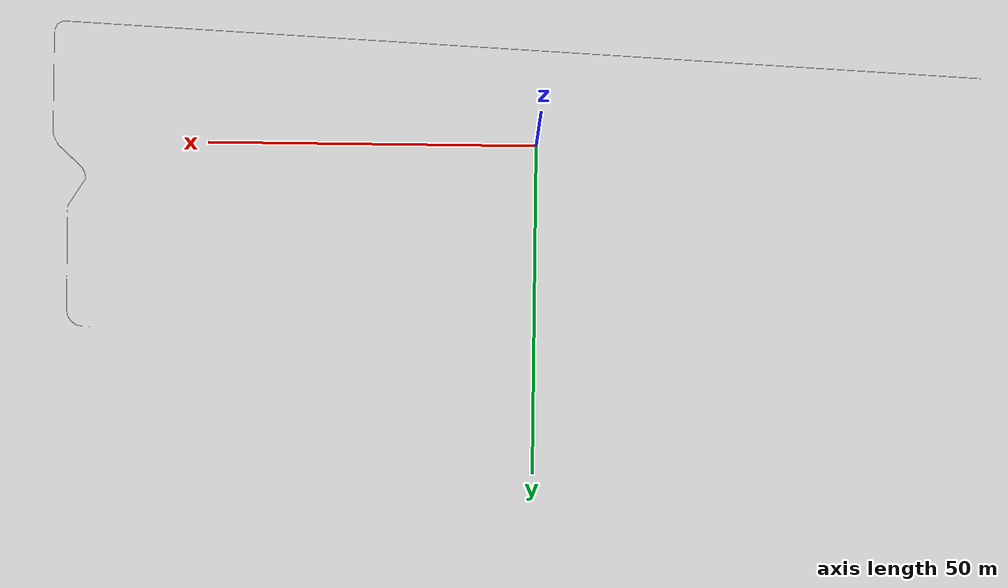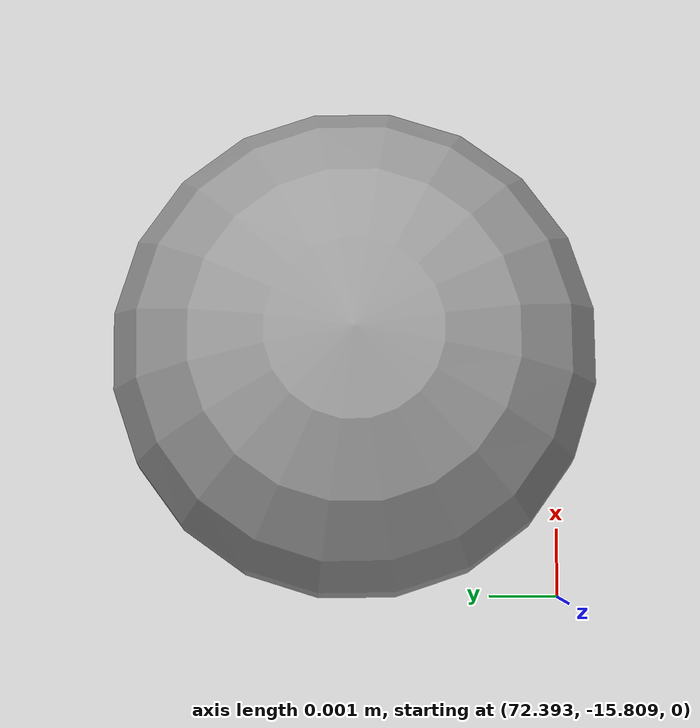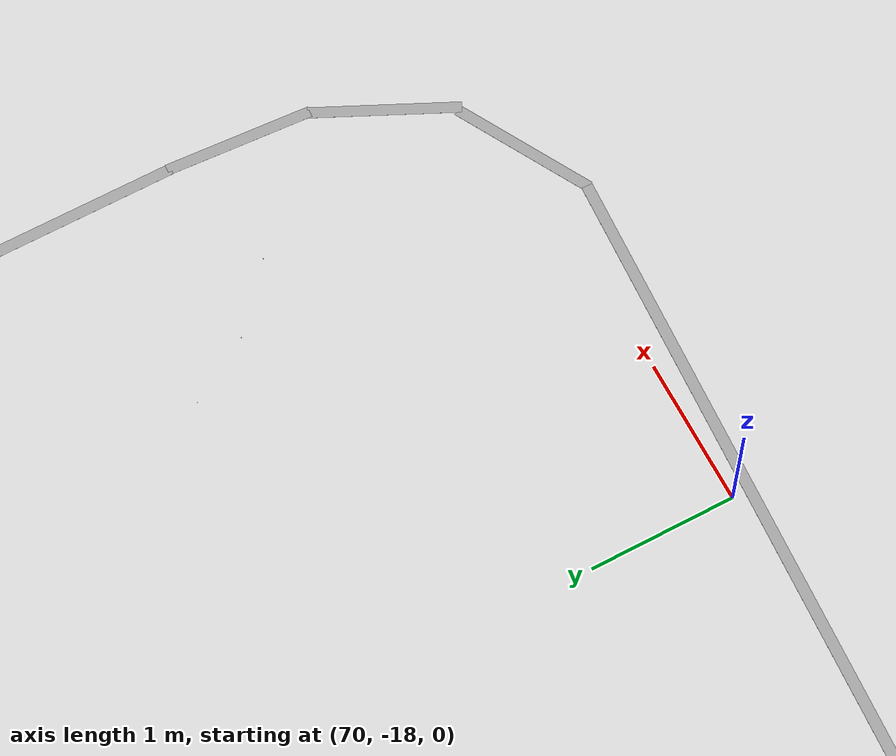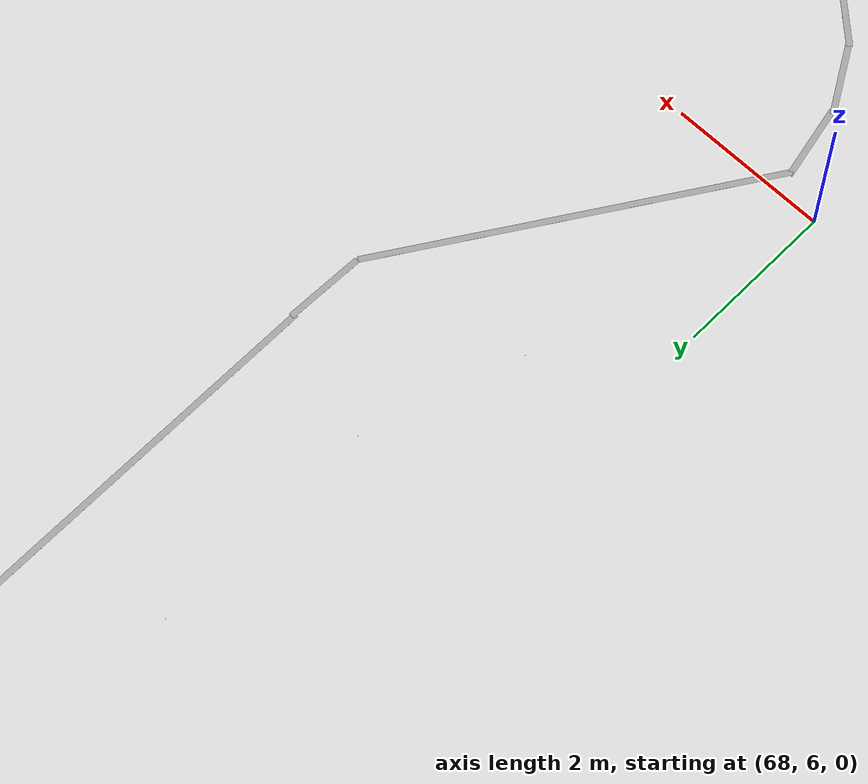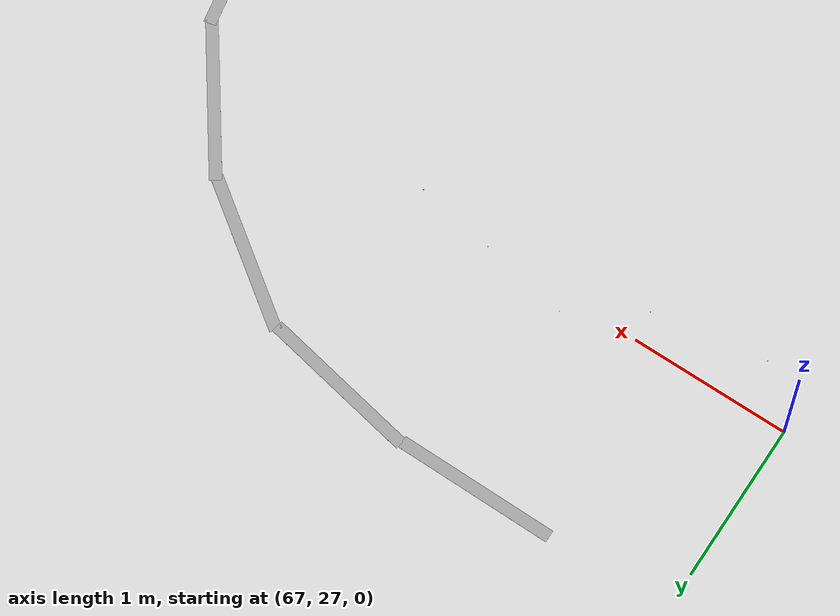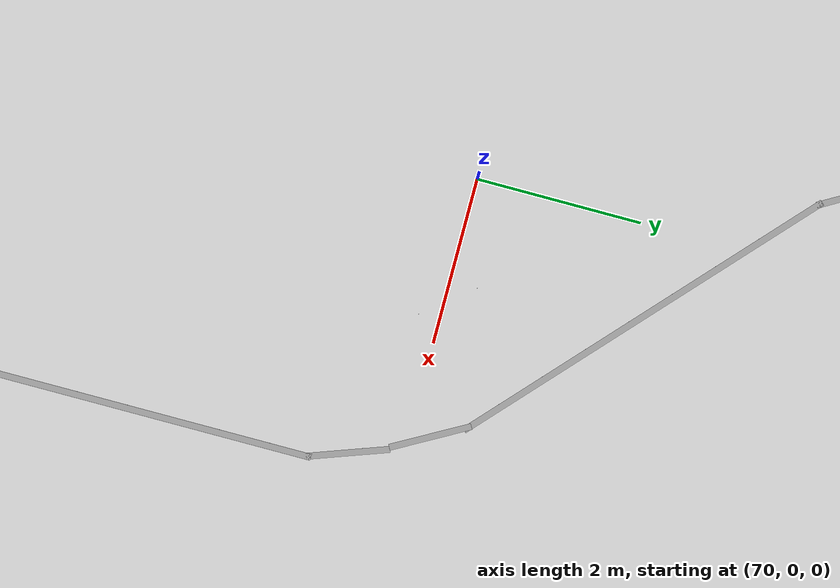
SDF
<sdf version="1.7">
 <world name="default">
  <light name="sun" type="directional">
   <pose>0 0 10 0 -0 0</pose>
   <diffuse>0.8 0.8 0.8 1</diffuse>
   <specular>0.2 0.2 0.2 1</specular>
   <attenuation>
    <range>1000</range>
    <constant>0.9</constant>
    <linear>0.01</linear>
    <quadratic>0.001</quadratic>
   </attenuation>
   <direction>-0.5 0.1 -0.9</direction>
   <spot><inner_angle>0</inner_angle><outer_angle>0</outer_angle><falloff>0</falloff></spot>
  </light>
  <model name="ground_plane">
   <static>1</static>
   <link name="link">
    <collision name="collision">
     <geometry><plane><normal>0 0 1</normal><size>100 100</size></plane></geometry>
     <surface>
      <contact><collide_bitmask>65535</collide_bitmask></contact>
      <friction><ode><mu>100</mu><mu2>50</mu2></ode></friction>
     </surface>
    </collision>
    <visual name="visual">
     <cast_shadows>0</cast_shadows>
     <geometry><plane><normal>0 0 1</normal><size>100 100</size></plane></geometry>
     <material>
      <script><uri>file://media/materials/scripts/gazebo.material</uri><name>Gazebo/Grey</name></script>
     </material>
    </visual>
   </link>
  </model>
  <gravity>0 0 -9.8</gravity>
  <magnetic_field>6e-06 2.3e-05 -4.2e-05</magnetic_field>
  <atmosphere type="adiabatic"/>
  <physics type="ode">
   <max_step_size>0.001</max_step_size>
   <real_time_factor>1</real_time_factor>
   <real_time_update_rate>1000</real_time_update_rate>
  </physics>
  <scene><ambient>0.4 0.4 0.4 1</ambient><background>0.7 0.7 0.7 1</background><shadows>1</shadows></scene>
  <spherical_coordinates>
   <surface_model>EARTH_WGS84</surface_model>
   <latitude_deg>0</latitude_deg>
   <longitude_deg>0</longitude_deg>
   <elevation>0</elevation>
   <heading_deg>0</heading_deg>
  </spherical_coordinates>
  <model name="whiteTape140ft">
   <link name="link_1">
    <inertial>
     <mass>0.00083454</mass>
     <inertia>
      <ixx>6.955e-05</ixx>
      <ixy>0</ixy>
      <ixz>0</ixz>
      <iyy>6.955e-05</iyy>
      <iyz>0</iyz>
      <izz>0.00013909</izz>
     </inertia>
    </inertial>
    <pose>-1.63246 -0.127798 -0 0 -0 0</pose>
    <visual name="visual">
     <geometry><box><size>0.0762 140 0.000831</size></box></geometry>
     <material>
      <lighting>1</lighting>
      <script><uri>file://media/materials/scripts/gazebo.material</uri><name>Gazebo/Grey</name></script>
      <shader type="normal_map_tangent_space"><normal_map>__default__</normal_map></shader>
      <ambient>0 0 0 1</ambient>
      <diffuse>0 0 0 1</diffuse>
      <specular>0.3 0.3 0.3 1</specular>
      <emissive>1 1 1 1</emissive>
     </material>
    </visual>
    <collision name="collision">
     <geometry><box><size>0.0762 140 0.000831</size></box></geometry>
     <surface>
      <friction>
       <ode><mu>1</mu><mu2>1</mu2><fdir1>0 0 0</fdir1><slip1>0</slip1><slip2>0</slip2></ode>
       <torsional>
        <coefficient>1</coefficient>
        <patch_radius>0</patch_radius>
        <surface_radius>0</surface_radius>
        <use_patch_radius>1</use_patch_radius>
        <ode><slip>0</slip></ode>
       </torsional>
      </friction>
      <bounce><restitution_coefficient>0</restitution_coefficient><threshold>1e+06</threshold></bounce>
      <contact>
       <collide_without_contact>0</collide_without_contact>
       <collide_without_contact_bitmask>1</collide_without_contact_bitmask>
       <collide_bitmask>1</collide_bitmask>
       <ode>
        <soft_cfm>0</soft_cfm>
        <soft_erp>0.2</soft_erp>
        <kp>1e+13</kp>
        <kd>1</kd>
        <max_vel>0.01</max_vel>
        <min_depth>0</min_depth>
       </ode>
       <bullet>
        <split_impulse>1</split_impulse>
        <split_impulse_penetration_threshold>-0.01</split_impulse_penetration_threshold>
        <soft_cfm>0</soft_cfm>
        <soft_erp>0.2</soft_erp>
        <kp>1e+13</kp>
        <kd>1</kd>
       </bullet>
      </contact>
     </surface>
    </collision>
   </link>
   <model name="ball_bearing">
    <link name="link">
     <pose>0 0 0.003 0 -0 0</pose>
     <inertial>
      <mass>0.0011</mass>
      <inertia>
       <ixx>3.96e-09</ixx>
       <ixy>0</ixy>
       <ixz>0</ixz>
       <iyy>3.96e-09</iyy>
       <iyz>0</iyz>
       <izz>3.96e-09</izz>
      </inertia>
     </inertial>
     <collision name="collision">
      <geometry><sphere><radius>0.003</radius></sphere></geometry>
      <surface>
       <contact>
        <poissons_ratio>0.305</poissons_ratio>
        <elastic_modulus>2e+11</elastic_modulus>
        <ode><kp>100000</kp><kd>100</kd><max_vel>100</max_vel><min_depth>0.001</min_depth></ode>
       </contact>
       <friction>
        <torsional>
         <coefficient>1</coefficient>
         <use_patch_radius>0</use_patch_radius>
         <surface_radius>0.01</surface_radius>
        </torsional>
       </friction>
      </surface>
     </collision>
     <visual name="visual">
      <geometry><sphere><radius>0.003</radius></sphere></geometry>
      <material>
       <script><uri>file://media/materials/scripts/gazebo.material</uri><name>Gazebo/Grey</name></script>
      </material>
     </visual>
     <velocity_decay><linear>0</linear><angular>0.005</angular></velocity_decay>
    </link>
    <pose>-3.19098 0.837722 0 0 -0 0</pose>
   </model>
   <static>0</static>
   <pose>2.34082 -13.0389 0.000406 0 -2.9e-05 1.51986</pose>
  </model>
  <model name="WhiteTape5M">
   <link name="link_1">
    <inertial>
     <mass>0.00083454</mass>
     <inertia>
      <ixx>6.955e-05</ixx>
      <ixy>0</ixy>
      <ixz>0</ixz>
      <iyy>6.955e-05</iyy>
      <iyz>0</iyz>
      <izz>0.00013909</izz>
     </inertia>
    </inertial>
    <pose>-1.63246 -0.127798 0 0 -0 0</pose>
    <visual name="visual">
     <geometry><box><size>0.0762 5 0.000831</size></box></geometry>
     <material>
      <lighting>1</lighting>
      <script><uri>file://media/materials/scripts/gazebo.material</uri><name>Gazebo/Grey</name></script>
      <shader type="normal_map_tangent_space"><normal_map>__default__</normal_map></shader>
      <ambient>0 0 0 1</ambient>
      <diffuse>0 0 0 1</diffuse>
      <specular>0.3 0.3 0.3 1</specular>
      <emissive>1 1 1 1</emissive>
     </material>
    </visual>
    <collision name="collision">
     <geometry><box><size>0.0762 5 0.000831</size></box></geometry>
     <surface>
      <friction>
       <ode><mu>1</mu><mu2>1</mu2><fdir1>0 0 0</fdir1><slip1>0</slip1><slip2>0</slip2></ode>
       <torsional>
        <coefficient>1</coefficient>
        <patch_radius>0</patch_radius>
        <surface_radius>0</surface_radius>
        <use_patch_radius>1</use_patch_radius>
        <ode><slip>0</slip></ode>
       </torsional>
      </friction>
      <bounce><restitution_coefficient>0</restitution_coefficient><threshold>1e+06</threshold></bounce>
      <contact>
       <collide_without_contact>0</collide_without_contact>
       <collide_without_contact_bitmask>1</collide_without_contact_bitmask>
       <collide_bitmask>1</collide_bitmask>
       <ode>
        <soft_cfm>0</soft_cfm>
        <soft_erp>0.2</soft_erp>
        <kp>1e+13</kp>
        <kd>1</kd>
        <max_vel>0.01</max_vel>
        <min_depth>0</min_depth>
       </ode>
       <bullet>
        <split_impulse>1</split_impulse>
        <split_impulse_penetration_threshold>-0.01</split_impulse_penetration_threshold>
        <soft_cfm>0</soft_cfm>
        <soft_erp>0.2</soft_erp>
        <kp>1e+13</kp>
        <kd>1</kd>
       </bullet>
      </contact>
     </surface>
    </collision>
   </link>
   <model name="ball_bearing">
    <link name="link">
     <pose>0 0 0.003 0 -0 0</pose>
     <inertial>
      <mass>0.0011</mass>
      <inertia>
       <ixx>3.96e-09</ixx>
       <ixy>0</ixy>
       <ixz>0</ixz>
       <iyy>3.96e-09</iyy>
       <iyz>0</iyz>
       <izz>3.96e-09</izz>
      </inertia>
     </inertial>
     <collision name="collision">
      <geometry><sphere><radius>0.003</radius></sphere></geometry>
      <surface>
       <contact>
        <poissons_ratio>0.305</poissons_ratio>
        <elastic_modulus>2e+11</elastic_modulus>
        <ode><kp>100000</kp><kd>100</kd><max_vel>100</max_vel><min_depth>0.001</min_depth></ode>
       </contact>
       <friction>
        <torsional>
         <coefficient>1</coefficient>
         <use_patch_radius>0</use_patch_radius>
         <surface_radius>0.01</surface_radius>
        </torsional>
       </friction>
      </surface>
     </collision>
     <visual name="visual">
      <geometry><sphere><radius>0.003</radius></sphere></geometry>
      <material>
       <script><uri>file://media/materials/scripts/gazebo.material</uri><name>Gazebo/Grey</name></script>
      </material>
     </visual>
     <velocity_decay><linear>0</linear><angular>0.005</angular></velocity_decay>
    </link>
    <pose>-3.19098 0.837722 0 0 -0 0</pose>
   </model>
   <static>0</static>
   <pose>75.2889 -13.3175 0 0 -0 0</pose>
  </model>
  <model name="myWhiteTape">
   <link name="link_1">
    <inertial>
     <mass>0.00083454</mass>
     <inertia>
      <ixx>6.955e-05</ixx>
      <ixy>0</ixy>
      <ixz>0</ixz>
      <iyy>6.955e-05</iyy>
      <iyz>0</iyz>
      <izz>0.00013909</izz>
     </inertia>
    </inertial>
    <pose>-1.63246 -0.127798 -0 0 -0 0</pose>
    <visual name="visual">
     <geometry><box><size>0.0762 1 0.000831</size></box></geometry>
     <material>
      <lighting>1</lighting>
      <script><uri>file://media/materials/scripts/gazebo.material</uri><name>Gazebo/Grey</name></script>
      <shader type="normal_map_tangent_space"><normal_map>__default__</normal_map></shader>
      <ambient>0 0 0 1</ambient>
      <diffuse>0 0 0 1</diffuse>
      <specular>0.3 0.3 0.3 1</specular>
      <emissive>1 1 1 1</emissive>
     </material>
    </visual>
    <collision name="collision">
     <geometry><box><size>0.0762 1 0.000831</size></box></geometry>
     <surface>
      <friction>
       <ode><mu>1</mu><mu2>1</mu2><fdir1>0 0 0</fdir1><slip1>0</slip1><slip2>0</slip2></ode>
       <torsional>
        <coefficient>1</coefficient>
        <patch_radius>0</patch_radius>
        <surface_radius>0</surface_radius>
        <use_patch_radius>1</use_patch_radius>
        <ode><slip>0</slip></ode>
       </torsional>
      </friction>
      <bounce><restitution_coefficient>0</restitution_coefficient><threshold>1e+06</threshold></bounce>
      <contact>
       <collide_without_contact>0</collide_without_contact>
       <collide_without_contact_bitmask>1</collide_without_contact_bitmask>
       <collide_bitmask>1</collide_bitmask>
       <ode>
        <soft_cfm>0</soft_cfm>
        <soft_erp>0.2</soft_erp>
        <kp>1e+13</kp>
        <kd>1</kd>
        <max_vel>0.01</max_vel>
        <min_depth>0</min_depth>
       </ode>
       <bullet>
        <split_impulse>1</split_impulse>
        <split_impulse_penetration_threshold>-0.01</split_impulse_penetration_threshold>
        <soft_cfm>0</soft_cfm>
        <soft_erp>0.2</soft_erp>
        <kp>1e+13</kp>
        <kd>1</kd>
       </bullet>
      </contact>
     </surface>
    </collision>
   </link>
   <model name="ball_bearing">
    <link name="link">
     <pose>0 0 0.003 0 -0 0</pose>
     <inertial>
      <mass>0.0011</mass>
      <inertia>
       <ixx>3.96e-09</ixx>
       <ixy>0</ixy>
       <ixz>0</ixz>
       <iyy>3.96e-09</iyy>
       <iyz>0</iyz>
       <izz>3.96e-09</izz>
      </inertia>
     </inertial>
     <collision name="collision">
      <geometry><sphere><radius>0.003</radius></sphere></geometry>
      <surface>
       <contact>
        <poissons_ratio>0.305</poissons_ratio>
        <elastic_modulus>2e+11</elastic_modulus>
        <ode><kp>100000</kp><kd>100</kd><max_vel>100</max_vel><min_depth>0.001</min_depth></ode>
       </contact>
       <friction>
        <torsional>
         <coefficient>1</coefficient>
         <use_patch_radius>0</use_patch_radius>
         <surface_radius>0.01</surface_radius>
        </torsional>
       </friction>
      </surface>
     </collision>
     <visual name="visual">
      <geometry><sphere><radius>0.003</radius></sphere></geometry>
      <material>
       <script><uri>file://media/materials/scripts/gazebo.material</uri><name>Gazebo/Grey</name></script>
      </material>
     </visual>
     <velocity_decay><linear>0</linear><angular>0.005</angular></velocity_decay>
    </link>
    <pose>-3.19098 0.837722 0 0 -0 0</pose>
   </model>
   <static>0</static>
   <pose>73.6205 -19.3768 0 0 0 -1.06756</pose>
  </model>
  <model name="myWhiteTape_0">
   <link name="link_1">
    <inertial>
     <mass>0.00083454</mass>
     <inertia>
      <ixx>6.955e-05</ixx>
      <ixy>0</ixy>
      <ixz>0</ixz>
      <iyy>6.955e-05</iyy>
      <iyz>0</iyz>
      <izz>0.00013909</izz>
     </inertia>
    </inertial>
    <pose>-1.63246 -0.127798 -0 0 -0 0</pose>
    <visual name="visual">
     <geometry><box><size>0.0762 1 0.000831</size></box></geometry>
     <material>
      <lighting>1</lighting>
      <script><uri>file://media/materials/scripts/gazebo.material</uri><name>Gazebo/Grey</name></script>
      <shader type="normal_map_tangent_space"><normal_map>__default__</normal_map></shader>
      <ambient>0 0 0 1</ambient>
      <diffuse>0 0 0 1</diffuse>
      <specular>0.3 0.3 0.3 1</specular>
      <emissive>1 1 1 1</emissive>
     </material>
    </visual>
    <collision name="collision">
     <geometry><box><size>0.0762 1 0.000831</size></box></geometry>
     <surface>
      <friction>
       <ode><mu>1</mu><mu2>1</mu2><fdir1>0 0 0</fdir1><slip1>0</slip1><slip2>0</slip2></ode>
       <torsional>
        <coefficient>1</coefficient>
        <patch_radius>0</patch_radius>
        <surface_radius>0</surface_radius>
        <use_patch_radius>1</use_patch_radius>
        <ode><slip>0</slip></ode>
       </torsional>
      </friction>
      <bounce><restitution_coefficient>0</restitution_coefficient><threshold>1e+06</threshold></bounce>
      <contact>
       <collide_without_contact>0</collide_without_contact>
       <collide_without_contact_bitmask>1</collide_without_contact_bitmask>
       <collide_bitmask>1</collide_bitmask>
       <ode>
        <soft_cfm>0</soft_cfm>
        <soft_erp>0.2</soft_erp>
        <kp>1e+13</kp>
        <kd>1</kd>
        <max_vel>0.01</max_vel>
        <min_depth>0</min_depth>
       </ode>
       <bullet>
        <split_impulse>1</split_impulse>
        <split_impulse_penetration_threshold>-0.01</split_impulse_penetration_threshold>
        <soft_cfm>0</soft_cfm>
        <soft_erp>0.2</soft_erp>
        <kp>1e+13</kp>
        <kd>1</kd>
       </bullet>
      </contact>
     </surface>
    </collision>
   </link>
   <model name="ball_bearing">
    <link name="link">
     <pose>0 0 0.003 0 -0 0</pose>
     <inertial>
      <mass>0.0011</mass>
      <inertia>
       <ixx>3.96e-09</ixx>
       <ixy>0</ixy>
       <ixz>0</ixz>
       <iyy>3.96e-09</iyy>
       <iyz>0</iyz>
       <izz>3.96e-09</izz>
      </inertia>
     </inertial>
     <collision name="collision">
      <geometry><sphere><radius>0.003</radius></sphere></geometry>
      <surface>
       <contact>
        <poissons_ratio>0.305</poissons_ratio>
        <elastic_modulus>2e+11</elastic_modulus>
        <ode><kp>100000</kp><kd>100</kd><max_vel>100</max_vel><min_depth>0.001</min_depth></ode>
       </contact>
       <friction>
        <torsional>
         <coefficient>1</coefficient>
         <use_patch_radius>0</use_patch_radius>
         <surface_radius>0.01</surface_radius>
        </torsional>
       </friction>
      </surface>
     </collision>
     <visual name="visual">
      <geometry><sphere><radius>0.003</radius></sphere></geometry>
      <material>
       <script><uri>file://media/materials/scripts/gazebo.material</uri><name>Gazebo/Grey</name></script>
      </material>
     </visual>
     <velocity_decay><linear>0</linear><angular>0.005</angular></velocity_decay>
    </link>
    <pose>-3.19098 0.837722 0 0 -0 0</pose>
   </model>
   <static>0</static>
   <pose>74.9097 -17.9429 0 0 0 -0.44787</pose>
  </model>
  <model name="myWhiteTape_1">
   <link name="link_1">
    <inertial>
     <mass>0.00083454</mass>
     <inertia>
      <ixx>6.955e-05</ixx>
      <ixy>0</ixy>
      <ixz>0</ixz>
      <iyy>6.955e-05</iyy>
      <iyz>0</iyz>
      <izz>0.00013909</izz>
     </inertia>
    </inertial>
    <pose>-1.63246 -0.127798 -0 0 -0 0</pose>
    <visual name="visual">
     <geometry><box><size>0.0762 1 0.000831</size></box></geometry>
     <material>
      <lighting>1</lighting>
      <script><uri>file://media/materials/scripts/gazebo.material</uri><name>Gazebo/Grey</name></script>
      <shader type="normal_map_tangent_space"><normal_map>__default__</normal_map></shader>
      <ambient>0 0 0 1</ambient>
      <diffuse>0 0 0 1</diffuse>
      <specular>0.3 0.3 0.3 1</specular>
      <emissive>1 1 1 1</emissive>
     </material>
    </visual>
    <collision name="collision">
     <geometry><box><size>0.0762 1 0.000831</size></box></geometry>
     <surface>
      <friction>
       <ode><mu>1</mu><mu2>1</mu2><fdir1>0 0 0</fdir1><slip1>0</slip1><slip2>0</slip2></ode>
       <torsional>
        <coefficient>1</coefficient>
        <patch_radius>0</patch_radius>
        <surface_radius>0</surface_radius>
        <use_patch_radius>1</use_patch_radius>
        <ode><slip>0</slip></ode>
       </torsional>
      </friction>
      <bounce><restitution_coefficient>0</restitution_coefficient><threshold>1e+06</threshold></bounce>
      <contact>
       <collide_without_contact>0</collide_without_contact>
       <collide_without_contact_bitmask>1</collide_without_contact_bitmask>
       <collide_bitmask>1</collide_bitmask>
       <ode>
        <soft_cfm>0</soft_cfm>
        <soft_erp>0.2</soft_erp>
        <kp>1e+13</kp>
        <kd>1</kd>
        <max_vel>0.01</max_vel>
        <min_depth>0</min_depth>
       </ode>
       <bullet>
        <split_impulse>1</split_impulse>
        <split_impulse_penetration_threshold>-0.01</split_impulse_penetration_threshold>
        <soft_cfm>0</soft_cfm>
        <soft_erp>0.2</soft_erp>
        <kp>1e+13</kp>
        <kd>1</kd>
       </bullet>
      </contact>
     </surface>
    </collision>
   </link>
   <model name="ball_bearing">
    <link name="link">
     <pose>0 0 0.003 0 -0 0</pose>
     <inertial>
      <mass>0.0011</mass>
      <inertia>
       <ixx>3.96e-09</ixx>
       <ixy>0</ixy>
       <ixz>0</ixz>
       <iyy>3.96e-09</iyy>
       <iyz>0</iyz>
       <izz>3.96e-09</izz>
      </inertia>
     </inertial>
     <collision name="collision">
      <geometry><sphere><radius>0.003</radius></sphere></geometry>
      <surface>
       <contact>
        <poissons_ratio>0.305</poissons_ratio>
        <elastic_modulus>2e+11</elastic_modulus>
        <ode><kp>100000</kp><kd>100</kd><max_vel>100</max_vel><min_depth>0.001</min_depth></ode>
       </contact>
       <friction>
        <torsional>
         <coefficient>1</coefficient>
         <use_patch_radius>0</use_patch_radius>
         <surface_radius>0.01</surface_radius>
        </torsional>
       </friction>
      </surface>
     </collision>
     <visual name="visual">
      <geometry><sphere><radius>0.003</radius></sphere></geometry>
      <material>
       <script><uri>file://media/materials/scripts/gazebo.material</uri><name>Gazebo/Grey</name></script>
      </material>
     </visual>
     <velocity_decay><linear>0</linear><angular>0.005</angular></velocity_decay>
    </link>
    <pose>-3.19098 0.837722 0 0 -0 0</pose>
   </model>
   <static>0</static>
   <pose>75.2667 -16.3918 0 0 0 -0.060678</pose>
  </model>
  <model name="WhiteTape5M_0">
   <link name="link_1">
    <inertial>
     <mass>0.00083454</mass>
     <inertia>
      <ixx>6.955e-05</ixx>
      <ixy>0</ixy>
      <ixz>0</ixz>
      <iyy>6.955e-05</iyy>
      <iyz>0</iyz>
      <izz>0.00013909</izz>
     </inertia>
    </inertial>
    <pose>-1.63246 -0.127798 0 0 -0 0</pose>
    <visual name="visual">
     <geometry><box><size>0.0762 5 0.000831</size></box></geometry>
     <material>
      <lighting>1</lighting>
      <script><uri>file://media/materials/scripts/gazebo.material</uri><name>Gazebo/Grey</name></script>
      <shader type="normal_map_tangent_space"><normal_map>__default__</normal_map></shader>
      <ambient>0 0 0 1</ambient>
      <diffuse>0 0 0 1</diffuse>
      <specular>0.3 0.3 0.3 1</specular>
      <emissive>1 1 1 1</emissive>
     </material>
    </visual>
    <collision name="collision">
     <geometry><box><size>0.0762 5 0.000831</size></box></geometry>
     <surface>
      <friction>
       <ode><mu>1</mu><mu2>1</mu2><fdir1>0 0 0</fdir1><slip1>0</slip1><slip2>0</slip2></ode>
       <torsional>
        <coefficient>1</coefficient>
        <patch_radius>0</patch_radius>
        <surface_radius>0</surface_radius>
        <use_patch_radius>1</use_patch_radius>
        <ode><slip>0</slip></ode>
       </torsional>
      </friction>
      <bounce><restitution_coefficient>0</restitution_coefficient><threshold>1e+06</threshold></bounce>
      <contact>
       <collide_without_contact>0</collide_without_contact>
       <collide_without_contact_bitmask>1</collide_without_contact_bitmask>
       <collide_bitmask>1</collide_bitmask>
       <ode>
        <soft_cfm>0</soft_cfm>
        <soft_erp>0.2</soft_erp>
        <kp>1e+13</kp>
        <kd>1</kd>
        <max_vel>0.01</max_vel>
        <min_depth>0</min_depth>
       </ode>
       <bullet>
        <split_impulse>1</split_impulse>
        <split_impulse_penetration_threshold>-0.01</split_impulse_penetration_threshold>
        <soft_cfm>0</soft_cfm>
        <soft_erp>0.2</soft_erp>
        <kp>1e+13</kp>
        <kd>1</kd>
       </bullet>
      </contact>
     </surface>
    </collision>
   </link>
   <model name="ball_bearing">
    <link name="link">
     <pose>0 0 0.003 0 -0 0</pose>
     <inertial>
      <mass>0.0011</mass>
      <inertia>
       <ixx>3.96e-09</ixx>
       <ixy>0</ixy>
       <ixz>0</ixz>
       <iyy>3.96e-09</iyy>
       <iyz>0</iyz>
       <izz>3.96e-09</izz>
      </inertia>
     </inertial>
     <collision name="collision">
      <geometry><sphere><radius>0.003</radius></sphere></geometry>
      <surface>
       <contact>
        <poissons_ratio>0.305</poissons_ratio>
        <elastic_modulus>2e+11</elastic_modulus>
        <ode><kp>100000</kp><kd>100</kd><max_vel>100</max_vel><min_depth>0.001</min_depth></ode>
       </contact>
       <friction>
        <torsional>
         <coefficient>1</coefficient>
         <use_patch_radius>0</use_patch_radius>
         <surface_radius>0.01</surface_radius>
        </torsional>
       </friction>
      </surface>
     </collision>
     <visual name="visual">
      <geometry><sphere><radius>0.003</radius></sphere></geometry>
      <material>
       <script><uri>file://media/materials/scripts/gazebo.material</uri><name>Gazebo/Grey</name></script>
      </material>
     </visual>
     <velocity_decay><linear>0</linear><angular>0.005</angular></velocity_decay>
    </link>
    <pose>-3.19098 0.837722 0 0 -0 0</pose>
   </model>
   <static>0</static>
   <pose>75.294 -8.39327 0 0 -0 0</pose>
  </model>
  <model name="WhiteTape5M_1">
   <link name="link_1">
    <inertial>
     <mass>0.00083454</mass>
     <inertia>
      <ixx>6.955e-05</ixx>
      <ixy>0</ixy>
      <ixz>0</ixz>
      <iyy>6.955e-05</iyy>
      <iyz>0</iyz>
      <izz>0.00013909</izz>
     </inertia>
    </inertial>
    <pose>-1.63246 -0.127798 0 0 -0 0</pose>
    <visual name="visual">
     <geometry><box><size>0.0762 5 0.000831</size></box></geometry>
     <material>
      <lighting>1</lighting>
      <script><uri>file://media/materials/scripts/gazebo.material</uri><name>Gazebo/Grey</name></script>
      <shader type="normal_map_tangent_space"><normal_map>__default__</normal_map></shader>
      <ambient>0 0 0 1</ambient>
      <diffuse>0 0 0 1</diffuse>
      <specular>0.3 0.3 0.3 1</specular>
      <emissive>1 1 1 1</emissive>
     </material>
    </visual>
    <collision name="collision">
     <geometry><box><size>0.0762 5 0.000831</size></box></geometry>
     <surface>
      <friction>
       <ode><mu>1</mu><mu2>1</mu2><fdir1>0 0 0</fdir1><slip1>0</slip1><slip2>0</slip2></ode>
       <torsional>
        <coefficient>1</coefficient>
        <patch_radius>0</patch_radius>
        <surface_radius>0</surface_radius>
        <use_patch_radius>1</use_patch_radius>
        <ode><slip>0</slip></ode>
       </torsional>
      </friction>
      <bounce><restitution_coefficient>0</restitution_coefficient><threshold>1e+06</threshold></bounce>
      <contact>
       <collide_without_contact>0</collide_without_contact>
       <collide_without_contact_bitmask>1</collide_without_contact_bitmask>
       <collide_bitmask>1</collide_bitmask>
       <ode>
        <soft_cfm>0</soft_cfm>
        <soft_erp>0.2</soft_erp>
        <kp>1e+13</kp>
        <kd>1</kd>
        <max_vel>0.01</max_vel>
        <min_depth>0</min_depth>
       </ode>
       <bullet>
        <split_impulse>1</split_impulse>
        <split_impulse_penetration_threshold>-0.01</split_impulse_penetration_threshold>
        <soft_cfm>0</soft_cfm>
        <soft_erp>0.2</soft_erp>
        <kp>1e+13</kp>
        <kd>1</kd>
       </bullet>
      </contact>
     </surface>
    </collision>
   </link>
   <model name="ball_bearing">
    <link name="link">
     <pose>0 0 0.003 0 -0 0</pose>
     <inertial>
      <mass>0.0011</mass>
      <inertia>
       <ixx>3.96e-09</ixx>
       <ixy>0</ixy>
       <ixz>0</ixz>
       <iyy>3.96e-09</iyy>
       <iyz>0</iyz>
       <izz>3.96e-09</izz>
      </inertia>
     </inertial>
     <collision name="collision">
      <geometry><sphere><radius>0.003</radius></sphere></geometry>
      <surface>
       <contact>
        <poissons_ratio>0.305</poissons_ratio>
        <elastic_modulus>2e+11</elastic_modulus>
        <ode><kp>100000</kp><kd>100</kd><max_vel>100</max_vel><min_depth>0.001</min_depth></ode>
       </contact>
       <friction>
        <torsional>
         <coefficient>1</coefficient>
         <use_patch_radius>0</use_patch_radius>
         <surface_radius>0.01</surface_radius>
        </torsional>
       </friction>
      </surface>
     </collision>
     <visual name="visual">
      <geometry><sphere><radius>0.003</radius></sphere></geometry>
      <material>
       <script><uri>file://media/materials/scripts/gazebo.material</uri><name>Gazebo/Grey</name></script>
      </material>
     </visual>
     <velocity_decay><linear>0</linear><angular>0.005</angular></velocity_decay>
    </link>
    <pose>-3.19098 0.837722 0 0 -0 0</pose>
   </model>
   <static>0</static>
   <pose>75.3026 -3.418 0 0 -0 0</pose>
  </model>
  <model name="myWhiteTape_2">
   <link name="link_1">
    <inertial>
     <mass>0.00083454</mass>
     <inertia>
      <ixx>6.955e-05</ixx>
      <ixy>0</ixy>
      <ixz>0</ixz>
      <iyy>6.955e-05</iyy>
      <iyz>0</iyz>
      <izz>0.00013909</izz>
     </inertia>
    </inertial>
    <pose>-1.63246 -0.127798 -0 0 -0 0</pose>
    <visual name="visual">
     <geometry><box><size>0.0762 1 0.000831</size></box></geometry>
     <material>
      <lighting>1</lighting>
      <script><uri>file://media/materials/scripts/gazebo.material</uri><name>Gazebo/Grey</name></script>
      <shader type="normal_map_tangent_space"><normal_map>__default__</normal_map></shader>
      <ambient>0 0 0 1</ambient>
      <diffuse>0 0 0 1</diffuse>
      <specular>0.3 0.3 0.3 1</specular>
      <emissive>1 1 1 1</emissive>
     </material>
    </visual>
    <collision name="collision">
     <geometry><box><size>0.0762 1 0.000831</size></box></geometry>
     <surface>
      <friction>
       <ode><mu>1</mu><mu2>1</mu2><fdir1>0 0 0</fdir1><slip1>0</slip1><slip2>0</slip2></ode>
       <torsional>
        <coefficient>1</coefficient>
        <patch_radius>0</patch_radius>
        <surface_radius>0</surface_radius>
        <use_patch_radius>1</use_patch_radius>
        <ode><slip>0</slip></ode>
       </torsional>
      </friction>
      <bounce><restitution_coefficient>0</restitution_coefficient><threshold>1e+06</threshold></bounce>
      <contact>
       <collide_without_contact>0</collide_without_contact>
       <collide_without_contact_bitmask>1</collide_without_contact_bitmask>
       <collide_bitmask>1</collide_bitmask>
       <ode>
        <soft_cfm>0</soft_cfm>
        <soft_erp>0.2</soft_erp>
        <kp>1e+13</kp>
        <kd>1</kd>
        <max_vel>0.01</max_vel>
        <min_depth>0</min_depth>
       </ode>
       <bullet>
        <split_impulse>1</split_impulse>
        <split_impulse_penetration_threshold>-0.01</split_impulse_penetration_threshold>
        <soft_cfm>0</soft_cfm>
        <soft_erp>0.2</soft_erp>
        <kp>1e+13</kp>
        <kd>1</kd>
       </bullet>
      </contact>
     </surface>
    </collision>
   </link>
   <model name="ball_bearing">
    <link name="link">
     <pose>0 0 0.003 0 -0 0</pose>
     <inertial>
      <mass>0.0011</mass>
      <inertia>
       <ixx>3.96e-09</ixx>
       <ixy>0</ixy>
       <ixz>0</ixz>
       <iyy>3.96e-09</iyy>
       <iyz>0</iyz>
       <izz>3.96e-09</izz>
      </inertia>
     </inertial>
     <collision name="collision">
      <geometry><sphere><radius>0.003</radius></sphere></geometry>
      <surface>
       <contact>
        <poissons_ratio>0.305</poissons_ratio>
        <elastic_modulus>2e+11</elastic_modulus>
        <ode><kp>100000</kp><kd>100</kd><max_vel>100</max_vel><min_depth>0.001</min_depth></ode>
       </contact>
       <friction>
        <torsional>
         <coefficient>1</coefficient>
         <use_patch_radius>0</use_patch_radius>
         <surface_radius>0.01</surface_radius>
        </torsional>
       </friction>
      </surface>
     </collision>
     <visual name="visual">
      <geometry><sphere><radius>0.003</radius></sphere></geometry>
      <material>
       <script><uri>file://media/materials/scripts/gazebo.material</uri><name>Gazebo/Grey</name></script>
      </material>
     </visual>
     <velocity_decay><linear>0</linear><angular>0.005</angular></velocity_decay>
    </link>
    <pose>-3.19098 0.837722 0 0 -0 0</pose>
   </model>
   <static>0</static>
   <pose>74.9987 0.03372 0 0 -0 0.344038</pose>
  </model>
  <model name="myWhiteTape_3">
   <link name="link_1">
    <inertial>
     <mass>0.00083454</mass>
     <inertia>
      <ixx>6.955e-05</ixx>
      <ixy>0</ixy>
      <ixz>0</ixz>
      <iyy>6.955e-05</iyy>
      <iyz>0</iyz>
      <izz>0.00013909</izz>
     </inertia>
    </inertial>
    <pose>-1.63246 -0.127798 -0 0 -0 0</pose>
    <visual name="visual">
     <geometry><box><size>0.0762 1 0.000831</size></box></geometry>
     <material>
      <lighting>1</lighting>
      <script><uri>file://media/materials/scripts/gazebo.material</uri><name>Gazebo/Grey</name></script>
      <shader type="normal_map_tangent_space"><normal_map>__default__</normal_map></shader>
      <ambient>0 0 0 1</ambient>
      <diffuse>0 0 0 1</diffuse>
      <specular>0.3 0.3 0.3 1</specular>
      <emissive>1 1 1 1</emissive>
     </material>
    </visual>
    <collision name="collision">
     <geometry><box><size>0.0762 1 0.000831</size></box></geometry>
     <surface>
      <friction>
       <ode><mu>1</mu><mu2>1</mu2><fdir1>0 0 0</fdir1><slip1>0</slip1><slip2>0</slip2></ode>
       <torsional>
        <coefficient>1</coefficient>
        <patch_radius>0</patch_radius>
        <surface_radius>0</surface_radius>
        <use_patch_radius>1</use_patch_radius>
        <ode><slip>0</slip></ode>
       </torsional>
      </friction>
      <bounce><restitution_coefficient>0</restitution_coefficient><threshold>1e+06</threshold></bounce>
      <contact>
       <collide_without_contact>0</collide_without_contact>
       <collide_without_contact_bitmask>1</collide_without_contact_bitmask>
       <collide_bitmask>1</collide_bitmask>
       <ode>
        <soft_cfm>0</soft_cfm>
        <soft_erp>0.2</soft_erp>
        <kp>1e+13</kp>
        <kd>1</kd>
        <max_vel>0.01</max_vel>
        <min_depth>0</min_depth>
       </ode>
       <bullet>
        <split_impulse>1</split_impulse>
        <split_impulse_penetration_threshold>-0.01</split_impulse_penetration_threshold>
        <soft_cfm>0</soft_cfm>
        <soft_erp>0.2</soft_erp>
        <kp>1e+13</kp>
        <kd>1</kd>
       </bullet>
      </contact>
     </surface>
    </collision>
   </link>
   <model name="ball_bearing">
    <link name="link">
     <pose>0 0 0.003 0 -0 0</pose>
     <inertial>
      <mass>0.0011</mass>
      <inertia>
       <ixx>3.96e-09</ixx>
       <ixy>0</ixy>
       <ixz>0</ixz>
       <iyy>3.96e-09</iyy>
       <iyz>0</iyz>
       <izz>3.96e-09</izz>
      </inertia>
     </inertial>
     <collision name="collision">
      <geometry><sphere><radius>0.003</radius></sphere></geometry>
      <surface>
       <contact>
        <poissons_ratio>0.305</poissons_ratio>
        <elastic_modulus>2e+11</elastic_modulus>
        <ode><kp>100000</kp><kd>100</kd><max_vel>100</max_vel><min_depth>0.001</min_depth></ode>
       </contact>
       <friction>
        <torsional>
         <coefficient>1</coefficient>
         <use_patch_radius>0</use_patch_radius>
         <surface_radius>0.01</surface_radius>
        </torsional>
       </friction>
      </surface>
     </collision>
     <visual name="visual">
      <geometry><sphere><radius>0.003</radius></sphere></geometry>
      <material>
       <script><uri>file://media/materials/scripts/gazebo.material</uri><name>Gazebo/Grey</name></script>
      </material>
     </visual>
     <velocity_decay><linear>0</linear><angular>0.005</angular></velocity_decay>
    </link>
    <pose>-3.19098 0.837722 0 0 -0 0</pose>
   </model>
   <static>0</static>
   <pose>74.437 1.15833 0 0 -0 0.509542</pose>
  </model>
  <model name="WhiteTape5M_2">
   <link name="link_1">
    <inertial>
     <mass>0.00083454</mass>
     <inertia>
      <ixx>6.955e-05</ixx>
      <ixy>0</ixy>
      <ixz>0</ixz>
      <iyy>6.955e-05</iyy>
      <iyz>0</iyz>
      <izz>0.00013909</izz>
     </inertia>
    </inertial>
    <pose>-1.63246 -0.127798 0 0 -0 0</pose>
    <visual name="visual">
     <geometry><box><size>0.0762 5 0.000831</size></box></geometry>
     <material>
      <lighting>1</lighting>
      <script><uri>file://media/materials/scripts/gazebo.material</uri><name>Gazebo/Grey</name></script>
      <shader type="normal_map_tangent_space"><normal_map>__default__</normal_map></shader>
      <ambient>0 0 0 1</ambient>
      <diffuse>0 0 0 1</diffuse>
      <specular>0.3 0.3 0.3 1</specular>
      <emissive>1 1 1 1</emissive>
     </material>
    </visual>
    <collision name="collision">
     <geometry><box><size>0.0762 5 0.000831</size></box></geometry>
     <surface>
      <friction>
       <ode><mu>1</mu><mu2>1</mu2><fdir1>0 0 0</fdir1><slip1>0</slip1><slip2>0</slip2></ode>
       <torsional>
        <coefficient>1</coefficient>
        <patch_radius>0</patch_radius>
        <surface_radius>0</surface_radius>
        <use_patch_radius>1</use_patch_radius>
        <ode><slip>0</slip></ode>
       </torsional>
      </friction>
      <bounce><restitution_coefficient>0</restitution_coefficient><threshold>1e+06</threshold></bounce>
      <contact>
       <collide_without_contact>0</collide_without_contact>
       <collide_without_contact_bitmask>1</collide_without_contact_bitmask>
       <collide_bitmask>1</collide_bitmask>
       <ode>
        <soft_cfm>0</soft_cfm>
        <soft_erp>0.2</soft_erp>
        <kp>1e+13</kp>
        <kd>1</kd>
        <max_vel>0.01</max_vel>
        <min_depth>0</min_depth>
       </ode>
       <bullet>
        <split_impulse>1</split_impulse>
        <split_impulse_penetration_threshold>-0.01</split_impulse_penetration_threshold>
        <soft_cfm>0</soft_cfm>
        <soft_erp>0.2</soft_erp>
        <kp>1e+13</kp>
        <kd>1</kd>
       </bullet>
      </contact>
     </surface>
    </collision>
   </link>
   <model name="ball_bearing">
    <link name="link">
     <pose>0 0 0.003 0 -0 0</pose>
     <inertial>
      <mass>0.0011</mass>
      <inertia>
       <ixx>3.96e-09</ixx>
       <ixy>0</ixy>
       <ixz>0</ixz>
       <iyy>3.96e-09</iyy>
       <iyz>0</iyz>
       <izz>3.96e-09</izz>
      </inertia>
     </inertial>
     <collision name="collision">
      <geometry><sphere><radius>0.003</radius></sphere></geometry>
      <surface>
       <contact>
        <poissons_ratio>0.305</poissons_ratio>
        <elastic_modulus>2e+11</elastic_modulus>
        <ode><kp>100000</kp><kd>100</kd><max_vel>100</max_vel><min_depth>0.001</min_depth></ode>
       </contact>
       <friction>
        <torsional>
         <coefficient>1</coefficient>
         <use_patch_radius>0</use_patch_radius>
         <surface_radius>0.01</surface_radius>
        </torsional>
       </friction>
      </surface>
     </collision>
     <visual name="visual">
      <geometry><sphere><radius>0.003</radius></sphere></geometry>
      <material>
       <script><uri>file://media/materials/scripts/gazebo.material</uri><name>Gazebo/Grey</name></script>
      </material>
     </visual>
     <velocity_decay><linear>0</linear><angular>0.005</angular></velocity_decay>
    </link>
    <pose>-3.19098 0.837722 0 0 -0 0</pose>
   </model>
   <static>0</static>
   <pose>72.0672 3.59695 0 0 -0 0.827226</pose>
  </model>
  <model name="myWhiteTape_3_clone">
   <link name="link_1">
    <inertial>
     <mass>0.00083454</mass>
     <inertia>
      <ixx>6.955e-05</ixx>
      <ixy>0</ixy>
      <ixz>0</ixz>
      <iyy>6.955e-05</iyy>
      <iyz>0</iyz>
      <izz>0.00013909</izz>
     </inertia>
    </inertial>
    <pose>-1.63246 -0.127798 -0 0 -0 0</pose>
    <visual name="visual">
     <geometry><box><size>0.0762 1 0.000831</size></box></geometry>
     <material>
      <lighting>1</lighting>
      <script><uri>file://media/materials/scripts/gazebo.material</uri><name>Gazebo/Grey</name></script>
      <shader type="normal_map_tangent_space"><normal_map>__default__</normal_map></shader>
      <ambient>0 0 0 1</ambient>
      <diffuse>0 0 0 1</diffuse>
      <specular>0.3 0.3 0.3 1</specular>
      <emissive>1 1 1 1</emissive>
     </material>
    </visual>
    <collision name="collision">
     <geometry><box><size>0.0762 1 0.000831</size></box></geometry>
     <surface>
      <friction>
       <ode><mu>1</mu><mu2>1</mu2><fdir1>0 0 0</fdir1><slip1>0</slip1><slip2>0</slip2></ode>
       <torsional>
        <coefficient>1</coefficient>
        <patch_radius>0</patch_radius>
        <surface_radius>0</surface_radius>
        <use_patch_radius>1</use_patch_radius>
        <ode><slip>0</slip></ode>
       </torsional>
      </friction>
      <bounce><restitution_coefficient>0</restitution_coefficient><threshold>1e+06</threshold></bounce>
      <contact>
       <collide_without_contact>0</collide_without_contact>
       <collide_without_contact_bitmask>1</collide_without_contact_bitmask>
       <collide_bitmask>1</collide_bitmask>
       <ode>
        <soft_cfm>0</soft_cfm>
        <soft_erp>0.2</soft_erp>
        <kp>1e+13</kp>
        <kd>1</kd>
        <max_vel>0.01</max_vel>
        <min_depth>0</min_depth>
       </ode>
       <bullet>
        <split_impulse>1</split_impulse>
        <split_impulse_penetration_threshold>-0.01</split_impulse_penetration_threshold>
        <soft_cfm>0</soft_cfm>
        <soft_erp>0.2</soft_erp>
        <kp>1e+13</kp>
        <kd>1</kd>
       </bullet>
      </contact>
     </surface>
    </collision>
   </link>
   <model name="ball_bearing">
    <link name="link">
     <pose>0 0 0.003 0 -0 0</pose>
     <inertial>
      <mass>0.0011</mass>
      <inertia>
       <ixx>3.96e-09</ixx>
       <ixy>0</ixy>
       <ixz>0</ixz>
       <iyy>3.96e-09</iyy>
       <iyz>0</iyz>
       <izz>3.96e-09</izz>
      </inertia>
     </inertial>
     <collision name="collision">
      <geometry><sphere><radius>0.003</radius></sphere></geometry>
      <surface>
       <contact>
        <poissons_ratio>0.305</poissons_ratio>
        <elastic_modulus>2e+11</elastic_modulus>
        <ode><kp>100000</kp><kd>100</kd><max_vel>100</max_vel><min_depth>0.001</min_depth></ode>
       </contact>
       <friction>
        <torsional>
         <coefficient>1</coefficient>
         <use_patch_radius>0</use_patch_radius>
         <surface_radius>0.01</surface_radius>
        </torsional>
       </friction>
      </surface>
     </collision>
     <visual name="visual">
      <geometry><sphere><radius>0.003</radius></sphere></geometry>
      <material>
       <script><uri>file://media/materials/scripts/gazebo.material</uri><name>Gazebo/Grey</name></script>
      </material>
     </visual>
     <velocity_decay><linear>0</linear><angular>0.005</angular></velocity_decay>
    </link>
    <pose>-3.19098 0.837722 0 0 -0 0</pose>
   </model>
   <static>0</static>
   <pose>70.365 5.30192 0 0 -0 0.524721</pose>
  </model>
  <model name="myWhiteTape_3_clone_clone">
   <link name="link_1">
    <inertial>
     <mass>0.00083454</mass>
     <inertia>
      <ixx>6.955e-05</ixx>
      <ixy>0</ixy>
      <ixz>0</ixz>
      <iyy>6.955e-05</iyy>
      <iyz>0</iyz>
      <izz>0.00013909</izz>
     </inertia>
    </inertial>
    <pose>-1.63246 -0.127798 -0 0 -0 0</pose>
    <visual name="visual">
     <geometry><box><size>0.0762 1 0.000831</size></box></geometry>
     <material>
      <lighting>1</lighting>
      <script><uri>file://media/materials/scripts/gazebo.material</uri><name>Gazebo/Grey</name></script>
      <shader type="normal_map_tangent_space"><normal_map>__default__</normal_map></shader>
      <ambient>0 0 0 1</ambient>
      <diffuse>0 0 0 1</diffuse>
      <specular>0.3 0.3 0.3 1</specular>
      <emissive>1 1 1 1</emissive>
     </material>
    </visual>
    <collision name="collision">
     <geometry><box><size>0.0762 1 0.000831</size></box></geometry>
     <surface>
      <friction>
       <ode><mu>1</mu><mu2>1</mu2><fdir1>0 0 0</fdir1><slip1>0</slip1><slip2>0</slip2></ode>
       <torsional>
        <coefficient>1</coefficient>
        <patch_radius>0</patch_radius>
        <surface_radius>0</surface_radius>
        <use_patch_radius>1</use_patch_radius>
        <ode><slip>0</slip></ode>
       </torsional>
      </friction>
      <bounce><restitution_coefficient>0</restitution_coefficient><threshold>1e+06</threshold></bounce>
      <contact>
       <collide_without_contact>0</collide_without_contact>
       <collide_without_contact_bitmask>1</collide_without_contact_bitmask>
       <collide_bitmask>1</collide_bitmask>
       <ode>
        <soft_cfm>0</soft_cfm>
        <soft_erp>0.2</soft_erp>
        <kp>1e+13</kp>
        <kd>1</kd>
        <max_vel>0.01</max_vel>
        <min_depth>0</min_depth>
       </ode>
       <bullet>
        <split_impulse>1</split_impulse>
        <split_impulse_penetration_threshold>-0.01</split_impulse_penetration_threshold>
        <soft_cfm>0</soft_cfm>
        <soft_erp>0.2</soft_erp>
        <kp>1e+13</kp>
        <kd>1</kd>
       </bullet>
      </contact>
     </surface>
    </collision>
   </link>
   <model name="ball_bearing">
    <link name="link">
     <pose>0 0 0.003 0 -0 0</pose>
     <inertial>
      <mass>0.0011</mass>
      <inertia>
       <ixx>3.96e-09</ixx>
       <ixy>0</ixy>
       <ixz>0</ixz>
       <iyy>3.96e-09</iyy>
       <iyz>0</iyz>
       <izz>3.96e-09</izz>
      </inertia>
     </inertial>
     <collision name="collision">
      <geometry><sphere><radius>0.003</radius></sphere></geometry>
      <surface>
       <contact>
        <poissons_ratio>0.305</poissons_ratio>
        <elastic_modulus>2e+11</elastic_modulus>
        <ode><kp>100000</kp><kd>100</kd><max_vel>100</max_vel><min_depth>0.001</min_depth></ode>
       </contact>
       <friction>
        <torsional>
         <coefficient>1</coefficient>
         <use_patch_radius>0</use_patch_radius>
         <surface_radius>0.01</surface_radius>
        </torsional>
       </friction>
      </surface>
     </collision>
     <visual name="visual">
      <geometry><sphere><radius>0.003</radius></sphere></geometry>
      <material>
       <script><uri>file://media/materials/scripts/gazebo.material</uri><name>Gazebo/Grey</name></script>
      </material>
     </visual>
     <velocity_decay><linear>0</linear><angular>0.005</angular></velocity_decay>
    </link>
    <pose>-3.19098 0.837722 0 0 -0 0</pose>
   </model>
   <static>0</static>
   <pose>70.2668 5.72299 0 0 -0 0.208981</pose>
  </model>
  <model name="WhiteTape5M_3">
   <link name="link_1">
    <inertial>
     <mass>0.00083454</mass>
     <inertia>
      <ixx>6.955e-05</ixx>
      <ixy>0</ixy>
      <ixz>0</ixz>
      <iyy>6.955e-05</iyy>
      <iyz>0</iyz>
      <izz>0.00013909</izz>
     </inertia>
    </inertial>
    <pose>-1.63246 -0.127798 0 0 -0 0</pose>
    <visual name="visual">
     <geometry><box><size>0.0762 5 0.000831</size></box></geometry>
     <material>
      <lighting>1</lighting>
      <script><uri>file://media/materials/scripts/gazebo.material</uri><name>Gazebo/Grey</name></script>
      <shader type="normal_map_tangent_space"><normal_map>__default__</normal_map></shader>
      <ambient>0 0 0 1</ambient>
      <diffuse>0 0 0 1</diffuse>
      <specular>0.3 0.3 0.3 1</specular>
      <emissive>1 1 1 1</emissive>
     </material>
    </visual>
    <collision name="collision">
     <geometry><box><size>0.0762 5 0.000831</size></box></geometry>
     <surface>
      <friction>
       <ode><mu>1</mu><mu2>1</mu2><fdir1>0 0 0</fdir1><slip1>0</slip1><slip2>0</slip2></ode>
       <torsional>
        <coefficient>1</coefficient>
        <patch_radius>0</patch_radius>
        <surface_radius>0</surface_radius>
        <use_patch_radius>1</use_patch_radius>
        <ode><slip>0</slip></ode>
       </torsional>
      </friction>
      <bounce><restitution_coefficient>0</restitution_coefficient><threshold>1e+06</threshold></bounce>
      <contact>
       <collide_without_contact>0</collide_without_contact>
       <collide_without_contact_bitmask>1</collide_without_contact_bitmask>
       <collide_bitmask>1</collide_bitmask>
       <ode>
        <soft_cfm>0</soft_cfm>
        <soft_erp>0.2</soft_erp>
        <kp>1e+13</kp>
        <kd>1</kd>
        <max_vel>0.01</max_vel>
        <min_depth>0</min_depth>
       </ode>
       <bullet>
        <split_impulse>1</split_impulse>
        <split_impulse_penetration_threshold>-0.01</split_impulse_penetration_threshold>
        <soft_cfm>0</soft_cfm>
        <soft_erp>0.2</soft_erp>
        <kp>1e+13</kp>
        <kd>1</kd>
       </bullet>
      </contact>
     </surface>
    </collision>
   </link>
   <model name="ball_bearing">
    <link name="link">
     <pose>0 0 0.003 0 -0 0</pose>
     <inertial>
      <mass>0.0011</mass>
      <inertia>
       <ixx>3.96e-09</ixx>
       <ixy>0</ixy>
       <ixz>0</ixz>
       <iyy>3.96e-09</iyy>
       <iyz>0</iyz>
       <izz>3.96e-09</izz>
      </inertia>
     </inertial>
     <collision name="collision">
      <geometry><sphere><radius>0.003</radius></sphere></geometry>
      <surface>
       <contact>
        <poissons_ratio>0.305</poissons_ratio>
        <elastic_modulus>2e+11</elastic_modulus>
        <ode><kp>100000</kp><kd>100</kd><max_vel>100</max_vel><min_depth>0.001</min_depth></ode>
       </contact>
       <friction>
        <torsional>
         <coefficient>1</coefficient>
         <use_patch_radius>0</use_patch_radius>
         <surface_radius>0.01</surface_radius>
        </torsional>
       </friction>
      </surface>
     </collision>
     <visual name="visual">
      <geometry><sphere><radius>0.003</radius></sphere></geometry>
      <material>
       <script><uri>file://media/materials/scripts/gazebo.material</uri><name>Gazebo/Grey</name></script>
      </material>
     </visual>
     <velocity_decay><linear>0</linear><angular>0.005</angular></velocity_decay>
    </link>
    <pose>-3.19098 0.837722 0 0 -0 0</pose>
   </model>
   <static>0</static>
   <pose>71.3966 7.01234 0 0 0 -0.574718</pose>
  </model>
  <model name="myWhiteTape_3_clone_clone_0">
   <link name="link_1">
    <inertial>
     <mass>0.00083454</mass>
     <inertia>
      <ixx>6.955e-05</ixx>
      <ixy>0</ixy>
      <ixz>0</ixz>
      <iyy>6.955e-05</iyy>
      <iyz>0</iyz>
      <izz>0.00013909</izz>
     </inertia>
    </inertial>
    <pose>-1.63246 -0.127798 -0 0 -0 0</pose>
    <visual name="visual">
     <geometry><box><size>0.0762 1 0.000831</size></box></geometry>
     <material>
      <lighting>1</lighting>
      <script><uri>file://media/materials/scripts/gazebo.material</uri><name>Gazebo/Grey</name></script>
      <shader type="normal_map_tangent_space"><normal_map>__default__</normal_map></shader>
      <ambient>0 0 0 1</ambient>
      <diffuse>0 0 0 1</diffuse>
      <specular>0.3 0.3 0.3 1</specular>
      <emissive>1 1 1 1</emissive>
     </material>
    </visual>
    <collision name="collision">
     <geometry><box><size>0.0762 1 0.000831</size></box></geometry>
     <surface>
      <friction>
       <ode><mu>1</mu><mu2>1</mu2><fdir1>0 0 0</fdir1><slip1>0</slip1><slip2>0</slip2></ode>
       <torsional>
        <coefficient>1</coefficient>
        <patch_radius>0</patch_radius>
        <surface_radius>0</surface_radius>
        <use_patch_radius>1</use_patch_radius>
        <ode><slip>0</slip></ode>
       </torsional>
      </friction>
      <bounce><restitution_coefficient>0</restitution_coefficient><threshold>1e+06</threshold></bounce>
      <contact>
       <collide_without_contact>0</collide_without_contact>
       <collide_without_contact_bitmask>1</collide_without_contact_bitmask>
       <collide_bitmask>1</collide_bitmask>
       <ode>
        <soft_cfm>0</soft_cfm>
        <soft_erp>0.2</soft_erp>
        <kp>1e+13</kp>
        <kd>1</kd>
        <max_vel>0.01</max_vel>
        <min_depth>0</min_depth>
       </ode>
       <bullet>
        <split_impulse>1</split_impulse>
        <split_impulse_penetration_threshold>-0.01</split_impulse_penetration_threshold>
        <soft_cfm>0</soft_cfm>
        <soft_erp>0.2</soft_erp>
        <kp>1e+13</kp>
        <kd>1</kd>
       </bullet>
      </contact>
     </surface>
    </collision>
   </link>
   <model name="ball_bearing">
    <link name="link">
     <pose>0 0 0.003 0 -0 0</pose>
     <inertial>
      <mass>0.0011</mass>
      <inertia>
       <ixx>3.96e-09</ixx>
       <ixy>0</ixy>
       <ixz>0</ixz>
       <iyy>3.96e-09</iyy>
       <iyz>0</iyz>
       <izz>3.96e-09</izz>
      </inertia>
     </inertial>
     <collision name="collision">
      <geometry><sphere><radius>0.003</radius></sphere></geometry>
      <surface>
       <contact>
        <poissons_ratio>0.305</poissons_ratio>
        <elastic_modulus>2e+11</elastic_modulus>
        <ode><kp>100000</kp><kd>100</kd><max_vel>100</max_vel><min_depth>0.001</min_depth></ode>
       </contact>
       <friction>
        <torsional>
         <coefficient>1</coefficient>
         <use_patch_radius>0</use_patch_radius>
         <surface_radius>0.01</surface_radius>
        </torsional>
       </friction>
      </surface>
     </collision>
     <visual name="visual">
      <geometry><sphere><radius>0.003</radius></sphere></geometry>
      <material>
       <script><uri>file://media/materials/scripts/gazebo.material</uri><name>Gazebo/Grey</name></script>
      </material>
     </visual>
     <velocity_decay><linear>0</linear><angular>0.005</angular></velocity_decay>
    </link>
    <pose>-3.19098 0.837722 0 0 -0 0</pose>
   </model>
   <static>0</static>
   <pose>72.9659 10.4777 0 0 0 -0.02882</pose>
  </model>
  <model name="WhiteTape5M_1_clone">
   <link name="link_1">
    <inertial>
     <mass>0.00083454</mass>
     <inertia>
      <ixx>6.955e-05</ixx>
      <ixy>0</ixy>
      <ixz>0</ixz>
      <iyy>6.955e-05</iyy>
      <iyz>0</iyz>
      <izz>0.00013909</izz>
     </inertia>
    </inertial>
    <pose>-1.63246 -0.127798 0 0 -0 0</pose>
    <visual name="visual">
     <geometry><box><size>0.0762 5 0.000831</size></box></geometry>
     <material>
      <lighting>1</lighting>
      <script><uri>file://media/materials/scripts/gazebo.material</uri><name>Gazebo/Grey</name></script>
      <shader type="normal_map_tangent_space"><normal_map>__default__</normal_map></shader>
      <ambient>0 0 0 1</ambient>
      <diffuse>0 0 0 1</diffuse>
      <specular>0.3 0.3 0.3 1</specular>
      <emissive>1 1 1 1</emissive>
     </material>
    </visual>
    <collision name="collision">
     <geometry><box><size>0.0762 5 0.000831</size></box></geometry>
     <surface>
      <friction>
       <ode><mu>1</mu><mu2>1</mu2><fdir1>0 0 0</fdir1><slip1>0</slip1><slip2>0</slip2></ode>
       <torsional>
        <coefficient>1</coefficient>
        <patch_radius>0</patch_radius>
        <surface_radius>0</surface_radius>
        <use_patch_radius>1</use_patch_radius>
        <ode><slip>0</slip></ode>
       </torsional>
      </friction>
      <bounce><restitution_coefficient>0</restitution_coefficient><threshold>1e+06</threshold></bounce>
      <contact>
       <collide_without_contact>0</collide_without_contact>
       <collide_without_contact_bitmask>1</collide_without_contact_bitmask>
       <collide_bitmask>1</collide_bitmask>
       <ode>
        <soft_cfm>0</soft_cfm>
        <soft_erp>0.2</soft_erp>
        <kp>1e+13</kp>
        <kd>1</kd>
        <max_vel>0.01</max_vel>
        <min_depth>0</min_depth>
       </ode>
       <bullet>
        <split_impulse>1</split_impulse>
        <split_impulse_penetration_threshold>-0.01</split_impulse_penetration_threshold>
        <soft_cfm>0</soft_cfm>
        <soft_erp>0.2</soft_erp>
        <kp>1e+13</kp>
        <kd>1</kd>
       </bullet>
      </contact>
     </surface>
    </collision>
   </link>
   <model name="ball_bearing">
    <link name="link">
     <pose>0 0 0.003 0 -0 0</pose>
     <inertial>
      <mass>0.0011</mass>
      <inertia>
       <ixx>3.96e-09</ixx>
       <ixy>0</ixy>
       <ixz>0</ixz>
       <iyy>3.96e-09</iyy>
       <iyz>0</iyz>
       <izz>3.96e-09</izz>
      </inertia>
     </inertial>
     <collision name="collision">
      <geometry><sphere><radius>0.003</radius></sphere></geometry>
      <surface>
       <contact>
        <poissons_ratio>0.305</poissons_ratio>
        <elastic_modulus>2e+11</elastic_modulus>
        <ode><kp>100000</kp><kd>100</kd><max_vel>100</max_vel><min_depth>0.001</min_depth></ode>
       </contact>
       <friction>
        <torsional>
         <coefficient>1</coefficient>
         <use_patch_radius>0</use_patch_radius>
         <surface_radius>0.01</surface_radius>
        </torsional>
       </friction>
      </surface>
     </collision>
     <visual name="visual">
      <geometry><sphere><radius>0.003</radius></sphere></geometry>
      <material>
       <script><uri>file://media/materials/scripts/gazebo.material</uri><name>Gazebo/Grey</name></script>
      </material>
     </visual>
     <velocity_decay><linear>0</linear><angular>0.005</angular></velocity_decay>
    </link>
    <pose>-3.19098 0.837722 0 0 -0 0</pose>
   </model>
   <static>0</static>
   <pose>72.9575 13.4765 0 0 -0 0</pose>
  </model>
  <model name="WhiteTape5M_1_clone_clone">
   <link name="link_1">
    <inertial>
     <mass>0.00083454</mass>
     <inertia>
      <ixx>6.955e-05</ixx>
      <ixy>0</ixy>
      <ixz>0</ixz>
      <iyy>6.955e-05</iyy>
      <iyz>0</iyz>
      <izz>0.00013909</izz>
     </inertia>
    </inertial>
    <pose>-1.63246 -0.127798 0 0 -0 0</pose>
    <visual name="visual">
     <geometry><box><size>0.0762 5 0.000831</size></box></geometry>
     <material>
      <lighting>1</lighting>
      <script><uri>file://media/materials/scripts/gazebo.material</uri><name>Gazebo/Grey</name></script>
      <shader type="normal_map_tangent_space"><normal_map>__default__</normal_map></shader>
      <ambient>0 0 0 1</ambient>
      <diffuse>0 0 0 1</diffuse>
      <specular>0.3 0.3 0.3 1</specular>
      <emissive>1 1 1 1</emissive>
     </material>
    </visual>
    <collision name="collision">
     <geometry><box><size>0.0762 5 0.000831</size></box></geometry>
     <surface>
      <friction>
       <ode><mu>1</mu><mu2>1</mu2><fdir1>0 0 0</fdir1><slip1>0</slip1><slip2>0</slip2></ode>
       <torsional>
        <coefficient>1</coefficient>
        <patch_radius>0</patch_radius>
        <surface_radius>0</surface_radius>
        <use_patch_radius>1</use_patch_radius>
        <ode><slip>0</slip></ode>
       </torsional>
      </friction>
      <bounce><restitution_coefficient>0</restitution_coefficient><threshold>1e+06</threshold></bounce>
      <contact>
       <collide_without_contact>0</collide_without_contact>
       <collide_without_contact_bitmask>1</collide_without_contact_bitmask>
       <collide_bitmask>1</collide_bitmask>
       <ode>
        <soft_cfm>0</soft_cfm>
        <soft_erp>0.2</soft_erp>
        <kp>1e+13</kp>
        <kd>1</kd>
        <max_vel>0.01</max_vel>
        <min_depth>0</min_depth>
       </ode>
       <bullet>
        <split_impulse>1</split_impulse>
        <split_impulse_penetration_threshold>-0.01</split_impulse_penetration_threshold>
        <soft_cfm>0</soft_cfm>
        <soft_erp>0.2</soft_erp>
        <kp>1e+13</kp>
        <kd>1</kd>
       </bullet>
      </contact>
     </surface>
    </collision>
   </link>
   <model name="ball_bearing">
    <link name="link">
     <pose>0 0 0.003 0 -0 0</pose>
     <inertial>
      <mass>0.0011</mass>
      <inertia>
       <ixx>3.96e-09</ixx>
       <ixy>0</ixy>
       <ixz>0</ixz>
       <iyy>3.96e-09</iyy>
       <iyz>0</iyz>
       <izz>3.96e-09</izz>
      </inertia>
     </inertial>
     <collision name="collision">
      <geometry><sphere><radius>0.003</radius></sphere></geometry>
      <surface>
       <contact>
        <poissons_ratio>0.305</poissons_ratio>
        <elastic_modulus>2e+11</elastic_modulus>
        <ode><kp>100000</kp><kd>100</kd><max_vel>100</max_vel><min_depth>0.001</min_depth></ode>
       </contact>
       <friction>
        <torsional>
         <coefficient>1</coefficient>
         <use_patch_radius>0</use_patch_radius>
         <surface_radius>0.01</surface_radius>
        </torsional>
       </friction>
      </surface>
     </collision>
     <visual name="visual">
      <geometry><sphere><radius>0.003</radius></sphere></geometry>
      <material>
       <script><uri>file://media/materials/scripts/gazebo.material</uri><name>Gazebo/Grey</name></script>
      </material>
     </visual>
     <velocity_decay><linear>0</linear><angular>0.005</angular></velocity_decay>
    </link>
    <pose>-3.19098 0.837722 0 0 -0 0</pose>
   </model>
   <static>0</static>
   <pose>72.9484 18.4101 0 0 -0 0</pose>
  </model>
  <model name="WhiteTape5M_1_clone_clone_0">
   <link name="link_1">
    <inertial>
     <mass>0.00083454</mass>
     <inertia>
      <ixx>6.955e-05</ixx>
      <ixy>0</ixy>
      <ixz>0</ixz>
      <iyy>6.955e-05</iyy>
      <iyz>0</iyz>
      <izz>0.00013909</izz>
     </inertia>
    </inertial>
    <pose>-1.63246 -0.127798 0 0 -0 0</pose>
    <visual name="visual">
     <geometry><box><size>0.0762 5 0.000831</size></box></geometry>
     <material>
      <lighting>1</lighting>
      <script><uri>file://media/materials/scripts/gazebo.material</uri><name>Gazebo/Grey</name></script>
      <shader type="normal_map_tangent_space"><normal_map>__default__</normal_map></shader>
      <ambient>0 0 0 1</ambient>
      <diffuse>0 0 0 1</diffuse>
      <specular>0.3 0.3 0.3 1</specular>
      <emissive>1 1 1 1</emissive>
     </material>
    </visual>
    <collision name="collision">
     <geometry><box><size>0.0762 5 0.000831</size></box></geometry>
     <surface>
      <friction>
       <ode><mu>1</mu><mu2>1</mu2><fdir1>0 0 0</fdir1><slip1>0</slip1><slip2>0</slip2></ode>
       <torsional>
        <coefficient>1</coefficient>
        <patch_radius>0</patch_radius>
        <surface_radius>0</surface_radius>
        <use_patch_radius>1</use_patch_radius>
        <ode><slip>0</slip></ode>
       </torsional>
      </friction>
      <bounce><restitution_coefficient>0</restitution_coefficient><threshold>1e+06</threshold></bounce>
      <contact>
       <collide_without_contact>0</collide_without_contact>
       <collide_without_contact_bitmask>1</collide_without_contact_bitmask>
       <collide_bitmask>1</collide_bitmask>
       <ode>
        <soft_cfm>0</soft_cfm>
        <soft_erp>0.2</soft_erp>
        <kp>1e+13</kp>
        <kd>1</kd>
        <max_vel>0.01</max_vel>
        <min_depth>0</min_depth>
       </ode>
       <bullet>
        <split_impulse>1</split_impulse>
        <split_impulse_penetration_threshold>-0.01</split_impulse_penetration_threshold>
        <soft_cfm>0</soft_cfm>
        <soft_erp>0.2</soft_erp>
        <kp>1e+13</kp>
        <kd>1</kd>
       </bullet>
      </contact>
     </surface>
    </collision>
   </link>
   <model name="ball_bearing">
    <link name="link">
     <pose>0 0 0.003 0 -0 0</pose>
     <inertial>
      <mass>0.0011</mass>
      <inertia>
       <ixx>3.96e-09</ixx>
       <ixy>0</ixy>
       <ixz>0</ixz>
       <iyy>3.96e-09</iyy>
       <iyz>0</iyz>
       <izz>3.96e-09</izz>
      </inertia>
     </inertial>
     <collision name="collision">
      <geometry><sphere><radius>0.003</radius></sphere></geometry>
      <surface>
       <contact>
        <poissons_ratio>0.305</poissons_ratio>
        <elastic_modulus>2e+11</elastic_modulus>
        <ode><kp>100000</kp><kd>100</kd><max_vel>100</max_vel><min_depth>0.001</min_depth></ode>
       </contact>
       <friction>
        <torsional>
         <coefficient>1</coefficient>
         <use_patch_radius>0</use_patch_radius>
         <surface_radius>0.01</surface_radius>
        </torsional>
       </friction>
      </surface>
     </collision>
     <visual name="visual">
      <geometry><sphere><radius>0.003</radius></sphere></geometry>
      <material>
       <script><uri>file://media/materials/scripts/gazebo.material</uri><name>Gazebo/Grey</name></script>
      </material>
     </visual>
     <velocity_decay><linear>0</linear><angular>0.005</angular></velocity_decay>
    </link>
    <pose>-3.19098 0.837722 0 0 -0 0</pose>
   </model>
   <static>0</static>
   <pose>72.9429 23.4077 0 0 -0 0</pose>
  </model>
  <model name="myWhiteTape_4">
   <link name="link_1">
    <inertial>
     <mass>0.00083454</mass>
     <inertia>
      <ixx>6.955e-05</ixx>
      <ixy>0</ixy>
      <ixz>0</ixz>
      <iyy>6.955e-05</iyy>
      <iyz>0</iyz>
      <izz>0.00013909</izz>
     </inertia>
    </inertial>
    <pose>-1.63246 -0.127798 -0 0 -0 0</pose>
    <visual name="visual">
     <geometry><box><size>0.0762 1 0.000831</size></box></geometry>
     <material>
      <lighting>1</lighting>
      <script><uri>file://media/materials/scripts/gazebo.material</uri><name>Gazebo/Grey</name></script>
      <shader type="normal_map_tangent_space"><normal_map>__default__</normal_map></shader>
      <ambient>0 0 0 1</ambient>
      <diffuse>0 0 0 1</diffuse>
      <specular>0.3 0.3 0.3 1</specular>
      <emissive>1 1 1 1</emissive>
     </material>
    </visual>
    <collision name="collision">
     <geometry><box><size>0.0762 1 0.000831</size></box></geometry>
     <surface>
      <friction>
       <ode><mu>1</mu><mu2>1</mu2><fdir1>0 0 0</fdir1><slip1>0</slip1><slip2>0</slip2></ode>
       <torsional>
        <coefficient>1</coefficient>
        <patch_radius>0</patch_radius>
        <surface_radius>0</surface_radius>
        <use_patch_radius>1</use_patch_radius>
        <ode><slip>0</slip></ode>
       </torsional>
      </friction>
      <bounce><restitution_coefficient>0</restitution_coefficient><threshold>1e+06</threshold></bounce>
      <contact>
       <collide_without_contact>0</collide_without_contact>
       <collide_without_contact_bitmask>1</collide_without_contact_bitmask>
       <collide_bitmask>1</collide_bitmask>
       <ode>
        <soft_cfm>0</soft_cfm>
        <soft_erp>0.2</soft_erp>
        <kp>1e+13</kp>
        <kd>1</kd>
        <max_vel>0.01</max_vel>
        <min_depth>0</min_depth>
       </ode>
       <bullet>
        <split_impulse>1</split_impulse>
        <split_impulse_penetration_threshold>-0.01</split_impulse_penetration_threshold>
        <soft_cfm>0</soft_cfm>
        <soft_erp>0.2</soft_erp>
        <kp>1e+13</kp>
        <kd>1</kd>
       </bullet>
      </contact>
     </surface>
    </collision>
   </link>
   <model name="ball_bearing">
    <link name="link">
     <pose>0 0 0.003 0 -0 0</pose>
     <inertial>
      <mass>0.0011</mass>
      <inertia>
       <ixx>3.96e-09</ixx>
       <ixy>0</ixy>
       <ixz>0</ixz>
       <iyy>3.96e-09</iyy>
       <iyz>0</iyz>
       <izz>3.96e-09</izz>
      </inertia>
     </inertial>
     <collision name="collision">
      <geometry><sphere><radius>0.003</radius></sphere></geometry>
      <surface>
       <contact>
        <poissons_ratio>0.305</poissons_ratio>
        <elastic_modulus>2e+11</elastic_modulus>
        <ode><kp>100000</kp><kd>100</kd><max_vel>100</max_vel><min_depth>0.001</min_depth></ode>
       </contact>
       <friction>
        <torsional>
         <coefficient>1</coefficient>
         <use_patch_radius>0</use_patch_radius>
         <surface_radius>0.01</surface_radius>
        </torsional>
       </friction>
      </surface>
     </collision>
     <visual name="visual">
      <geometry><sphere><radius>0.003</radius></sphere></geometry>
      <material>
       <script><uri>file://media/materials/scripts/gazebo.material</uri><name>Gazebo/Grey</name></script>
      </material>
     </visual>
     <velocity_decay><linear>0</linear><angular>0.005</angular></velocity_decay>
    </link>
    <pose>-3.19098 0.837722 0 0 -0 0</pose>
   </model>
   <static>0</static>
   <pose>72.8019 26.6598 0 0 -0 0.181676</pose>
  </model>
  <model name="myWhiteTape_4_clone">
   <link name="link_1">
    <inertial>
     <mass>0.00083454</mass>
     <inertia>
      <ixx>6.955e-05</ixx>
      <ixy>0</ixy>
      <ixz>0</ixz>
      <iyy>6.955e-05</iyy>
      <iyz>0</iyz>
      <izz>0.00013909</izz>
     </inertia>
    </inertial>
    <pose>-1.63246 -0.127798 -0 0 -0 0</pose>
    <visual name="visual">
     <geometry><box><size>0.0762 1 0.000831</size></box></geometry>
     <material>
      <lighting>1</lighting>
      <script><uri>file://media/materials/scripts/gazebo.material</uri><name>Gazebo/Grey</name></script>
      <shader type="normal_map_tangent_space"><normal_map>__default__</normal_map></shader>
      <ambient>0 0 0 1</ambient>
      <diffuse>0 0 0 1</diffuse>
      <specular>0.3 0.3 0.3 1</specular>
      <emissive>1 1 1 1</emissive>
     </material>
    </visual>
    <collision name="collision">
     <geometry><box><size>0.0762 1 0.000831</size></box></geometry>
     <surface>
      <friction>
       <ode><mu>1</mu><mu2>1</mu2><fdir1>0 0 0</fdir1><slip1>0</slip1><slip2>0</slip2></ode>
       <torsional>
        <coefficient>1</coefficient>
        <patch_radius>0</patch_radius>
        <surface_radius>0</surface_radius>
        <use_patch_radius>1</use_patch_radius>
        <ode><slip>0</slip></ode>
       </torsional>
      </friction>
      <bounce><restitution_coefficient>0</restitution_coefficient><threshold>1e+06</threshold></bounce>
      <contact>
       <collide_without_contact>0</collide_without_contact>
       <collide_without_contact_bitmask>1</collide_without_contact_bitmask>
       <collide_bitmask>1</collide_bitmask>
       <ode>
        <soft_cfm>0</soft_cfm>
        <soft_erp>0.2</soft_erp>
        <kp>1e+13</kp>
        <kd>1</kd>
        <max_vel>0.01</max_vel>
        <min_depth>0</min_depth>
       </ode>
       <bullet>
        <split_impulse>1</split_impulse>
        <split_impulse_penetration_threshold>-0.01</split_impulse_penetration_threshold>
        <soft_cfm>0</soft_cfm>
        <soft_erp>0.2</soft_erp>
        <kp>1e+13</kp>
        <kd>1</kd>
       </bullet>
      </contact>
     </surface>
    </collision>
   </link>
   <model name="ball_bearing">
    <link name="link">
     <pose>0 0 0.003 0 -0 0</pose>
     <inertial>
      <mass>0.0011</mass>
      <inertia>
       <ixx>3.96e-09</ixx>
       <ixy>0</ixy>
       <ixz>0</ixz>
       <iyy>3.96e-09</iyy>
       <iyz>0</iyz>
       <izz>3.96e-09</izz>
      </inertia>
     </inertial>
     <collision name="collision">
      <geometry><sphere><radius>0.003</radius></sphere></geometry>
      <surface>
       <contact>
        <poissons_ratio>0.305</poissons_ratio>
        <elastic_modulus>2e+11</elastic_modulus>
        <ode><kp>100000</kp><kd>100</kd><max_vel>100</max_vel><min_depth>0.001</min_depth></ode>
       </contact>
       <friction>
        <torsional>
         <coefficient>1</coefficient>
         <use_patch_radius>0</use_patch_radius>
         <surface_radius>0.01</surface_radius>
        </torsional>
       </friction>
      </surface>
     </collision>
     <visual name="visual">
      <geometry><sphere><radius>0.003</radius></sphere></geometry>
      <material>
       <script><uri>file://media/materials/scripts/gazebo.material</uri><name>Gazebo/Grey</name></script>
      </material>
     </visual>
     <velocity_decay><linear>0</linear><angular>0.005</angular></velocity_decay>
    </link>
    <pose>-3.19098 0.837722 0 0 -0 0</pose>
   </model>
   <static>0</static>
   <pose>72.0946 28.1644 0 0 -0 0.619418</pose>
  </model>
  <model name="myWhiteTape_4_clone_0">
   <link name="link_1">
    <inertial>
     <mass>0.00083454</mass>
     <inertia>
      <ixx>6.955e-05</ixx>
      <ixy>0</ixy>
      <ixz>0</ixz>
      <iyy>6.955e-05</iyy>
      <iyz>0</iyz>
      <izz>0.00013909</izz>
     </inertia>
    </inertial>
    <pose>-1.63246 -0.127798 -0 0 -0 0</pose>
    <visual name="visual">
     <geometry><box><size>0.0762 1 0.000831</size></box></geometry>
     <material>
      <lighting>1</lighting>
      <script><uri>file://media/materials/scripts/gazebo.material</uri><name>Gazebo/Grey</name></script>
      <shader type="normal_map_tangent_space"><normal_map>__default__</normal_map></shader>
      <ambient>0 0 0 1</ambient>
      <diffuse>0 0 0 1</diffuse>
      <specular>0.3 0.3 0.3 1</specular>
      <emissive>1 1 1 1</emissive>
     </material>
    </visual>
    <collision name="collision">
     <geometry><box><size>0.0762 1 0.000831</size></box></geometry>
     <surface>
      <friction>
       <ode><mu>1</mu><mu2>1</mu2><fdir1>0 0 0</fdir1><slip1>0</slip1><slip2>0</slip2></ode>
       <torsional>
        <coefficient>1</coefficient>
        <patch_radius>0</patch_radius>
        <surface_radius>0</surface_radius>
        <use_patch_radius>1</use_patch_radius>
        <ode><slip>0</slip></ode>
       </torsional>
      </friction>
      <bounce><restitution_coefficient>0</restitution_coefficient><threshold>1e+06</threshold></bounce>
      <contact>
       <collide_without_contact>0</collide_without_contact>
       <collide_without_contact_bitmask>1</collide_without_contact_bitmask>
       <collide_bitmask>1</collide_bitmask>
       <ode>
        <soft_cfm>0</soft_cfm>
        <soft_erp>0.2</soft_erp>
        <kp>1e+13</kp>
        <kd>1</kd>
        <max_vel>0.01</max_vel>
        <min_depth>0</min_depth>
       </ode>
       <bullet>
        <split_impulse>1</split_impulse>
        <split_impulse_penetration_threshold>-0.01</split_impulse_penetration_threshold>
        <soft_cfm>0</soft_cfm>
        <soft_erp>0.2</soft_erp>
        <kp>1e+13</kp>
        <kd>1</kd>
       </bullet>
      </contact>
     </surface>
    </collision>
   </link>
   <model name="ball_bearing">
    <link name="link">
     <pose>0 0 0.003 0 -0 0</pose>
     <inertial>
      <mass>0.0011</mass>
      <inertia>
       <ixx>3.96e-09</ixx>
       <ixy>0</ixy>
       <ixz>0</ixz>
       <iyy>3.96e-09</iyy>
       <iyz>0</iyz>
       <izz>3.96e-09</izz>
      </inertia>
     </inertial>
     <collision name="collision">
      <geometry><sphere><radius>0.003</radius></sphere></geometry>
      <surface>
       <contact>
        <poissons_ratio>0.305</poissons_ratio>
        <elastic_modulus>2e+11</elastic_modulus>
        <ode><kp>100000</kp><kd>100</kd><max_vel>100</max_vel><min_depth>0.001</min_depth></ode>
       </contact>
       <friction>
        <torsional>
         <coefficient>1</coefficient>
         <use_patch_radius>0</use_patch_radius>
         <surface_radius>0.01</surface_radius>
        </torsional>
       </friction>
      </surface>
     </collision>
     <visual name="visual">
      <geometry><sphere><radius>0.003</radius></sphere></geometry>
      <material>
       <script><uri>file://media/materials/scripts/gazebo.material</uri><name>Gazebo/Grey</name></script>
      </material>
     </visual>
     <velocity_decay><linear>0</linear><angular>0.005</angular></velocity_decay>
    </link>
    <pose>-3.19098 0.837722 0 0 -0 0</pose>
   </model>
   <static>0</static>
   <pose>71.0099 29.1854 0 0 -0 0.942517</pose>
  </model>
  <model name="myWhiteTape_4_clone_1">
   <link name="link_1">
    <inertial>
     <mass>0.00083454</mass>
     <inertia>
      <ixx>6.955e-05</ixx>
      <ixy>0</ixy>
      <ixz>0</ixz>
      <iyy>6.955e-05</iyy>
      <iyz>0</iyz>
      <izz>0.00013909</izz>
     </inertia>
    </inertial>
    <pose>-1.63246 -0.127798 -0 0 -0 0</pose>
    <visual name="visual">
     <geometry><box><size>0.0762 1 0.000831</size></box></geometry>
     <material>
      <lighting>1</lighting>
      <script><uri>file://media/materials/scripts/gazebo.material</uri><name>Gazebo/Grey</name></script>
      <shader type="normal_map_tangent_space"><normal_map>__default__</normal_map></shader>
      <ambient>0 0 0 1</ambient>
      <diffuse>0 0 0 1</diffuse>
      <specular>0.3 0.3 0.3 1</specular>
      <emissive>1 1 1 1</emissive>
     </material>
    </visual>
    <collision name="collision">
     <geometry><box><size>0.0762 1 0.000831</size></box></geometry>
     <surface>
      <friction>
       <ode><mu>1</mu><mu2>1</mu2><fdir1>0 0 0</fdir1><slip1>0</slip1><slip2>0</slip2></ode>
       <torsional>
        <coefficient>1</coefficient>
        <patch_radius>0</patch_radius>
        <surface_radius>0</surface_radius>
        <use_patch_radius>1</use_patch_radius>
        <ode><slip>0</slip></ode>
       </torsional>
      </friction>
      <bounce><restitution_coefficient>0</restitution_coefficient><threshold>1e+06</threshold></bounce>
      <contact>
       <collide_without_contact>0</collide_without_contact>
       <collide_without_contact_bitmask>1</collide_without_contact_bitmask>
       <collide_bitmask>1</collide_bitmask>
       <ode>
        <soft_cfm>0</soft_cfm>
        <soft_erp>0.2</soft_erp>
        <kp>1e+13</kp>
        <kd>1</kd>
        <max_vel>0.01</max_vel>
        <min_depth>0</min_depth>
       </ode>
       <bullet>
        <split_impulse>1</split_impulse>
        <split_impulse_penetration_threshold>-0.01</split_impulse_penetration_threshold>
        <soft_cfm>0</soft_cfm>
        <soft_erp>0.2</soft_erp>
        <kp>1e+13</kp>
        <kd>1</kd>
       </bullet>
      </contact>
     </surface>
    </collision>
   </link>
   <model name="ball_bearing">
    <link name="link">
     <pose>0 0 0.003 0 -0 0</pose>
     <inertial>
      <mass>0.0011</mass>
      <inertia>
       <ixx>3.96e-09</ixx>
       <ixy>0</ixy>
       <ixz>0</ixz>
       <iyy>3.96e-09</iyy>
       <iyz>0</iyz>
       <izz>3.96e-09</izz>
      </inertia>
     </inertial>
     <collision name="collision">
      <geometry><sphere><radius>0.003</radius></sphere></geometry>
      <surface>
       <contact>
        <poissons_ratio>0.305</poissons_ratio>
        <elastic_modulus>2e+11</elastic_modulus>
        <ode><kp>100000</kp><kd>100</kd><max_vel>100</max_vel><min_depth>0.001</min_depth></ode>
       </contact>
       <friction>
        <torsional>
         <coefficient>1</coefficient>
         <use_patch_radius>0</use_patch_radius>
         <surface_radius>0.01</surface_radius>
        </torsional>
       </friction>
      </surface>
     </collision>
     <visual name="visual">
      <geometry><sphere><radius>0.003</radius></sphere></geometry>
      <material>
       <script><uri>file://media/materials/scripts/gazebo.material</uri><name>Gazebo/Grey</name></script>
      </material>
     </visual>
     <velocity_decay><linear>0</linear><angular>0.005</angular></velocity_decay>
    </link>
    <pose>-3.19098 0.837722 0 0 -0 0</pose>
   </model>
   <static>0</static>
   <pose>69.4576 29.783 0 0 -0 1.37597</pose>
  </model>
  <model name="myWhiteTape_4_clone_2">
   <link name="link_1">
    <inertial>
     <mass>0.00083454</mass>
     <inertia>
      <ixx>6.955e-05</ixx>
      <ixy>0</ixy>
      <ixz>0</ixz>
      <iyy>6.955e-05</iyy>
      <iyz>0</iyz>
      <izz>0.00013909</izz>
     </inertia>
    </inertial>
    <pose>-1.63246 -0.127798 -0 0 -0 0</pose>
    <visual name="visual">
     <geometry><box><size>0.0762 1 0.000831</size></box></geometry>
     <material>
      <lighting>1</lighting>
      <script><uri>file://media/materials/scripts/gazebo.material</uri><name>Gazebo/Grey</name></script>
      <shader type="normal_map_tangent_space"><normal_map>__default__</normal_map></shader>
      <ambient>0 0 0 1</ambient>
      <diffuse>0 0 0 1</diffuse>
      <specular>0.3 0.3 0.3 1</specular>
      <emissive>1 1 1 1</emissive>
     </material>
    </visual>
    <collision name="collision">
     <geometry><box><size>0.0762 1 0.000831</size></box></geometry>
     <surface>
      <friction>
       <ode><mu>1</mu><mu2>1</mu2><fdir1>0 0 0</fdir1><slip1>0</slip1><slip2>0</slip2></ode>
       <torsional>
        <coefficient>1</coefficient>
        <patch_radius>0</patch_radius>
        <surface_radius>0</surface_radius>
        <use_patch_radius>1</use_patch_radius>
        <ode><slip>0</slip></ode>
       </torsional>
      </friction>
      <bounce><restitution_coefficient>0</restitution_coefficient><threshold>1e+06</threshold></bounce>
      <contact>
       <collide_without_contact>0</collide_without_contact>
       <collide_without_contact_bitmask>1</collide_without_contact_bitmask>
       <collide_bitmask>1</collide_bitmask>
       <ode>
        <soft_cfm>0</soft_cfm>
        <soft_erp>0.2</soft_erp>
        <kp>1e+13</kp>
        <kd>1</kd>
        <max_vel>0.01</max_vel>
        <min_depth>0</min_depth>
       </ode>
       <bullet>
        <split_impulse>1</split_impulse>
        <split_impulse_penetration_threshold>-0.01</split_impulse_penetration_threshold>
        <soft_cfm>0</soft_cfm>
        <soft_erp>0.2</soft_erp>
        <kp>1e+13</kp>
        <kd>1</kd>
       </bullet>
      </contact>
     </surface>
    </collision>
   </link>
   <model name="ball_bearing">
    <link name="link">
     <pose>0 0 0.003 0 -0 0</pose>
     <inertial>
      <mass>0.0011</mass>
      <inertia>
       <ixx>3.96e-09</ixx>
       <ixy>0</ixy>
       <ixz>0</ixz>
       <iyy>3.96e-09</iyy>
       <iyz>0</iyz>
       <izz>3.96e-09</izz>
      </inertia>
     </inertial>
     <collision name="collision">
      <geometry><sphere><radius>0.003</radius></sphere></geometry>
      <surface>
       <contact>
        <poissons_ratio>0.305</poissons_ratio>
        <elastic_modulus>2e+11</elastic_modulus>
        <ode><kp>100000</kp><kd>100</kd><max_vel>100</max_vel><min_depth>0.001</min_depth></ode>
       </contact>
       <friction>
        <torsional>
         <coefficient>1</coefficient>
         <use_patch_radius>0</use_patch_radius>
         <surface_radius>0.01</surface_radius>
        </torsional>
       </friction>
      </surface>
     </collision>
     <visual name="visual">
      <geometry><sphere><radius>0.003</radius></sphere></geometry>
      <material>
       <script><uri>file://media/materials/scripts/gazebo.material</uri><name>Gazebo/Grey</name></script>
      </material>
     </visual>
     <velocity_decay><linear>0</linear><angular>0.005</angular></velocity_decay>
    </link>
    <pose>-3.19098 0.837722 0 0 -0 0</pose>
   </model>
   <static>0</static>
   <pose>68.1658 29.8777 0 0 -0 1.56266</pose>
  </model>
 </world>
</sdf>
